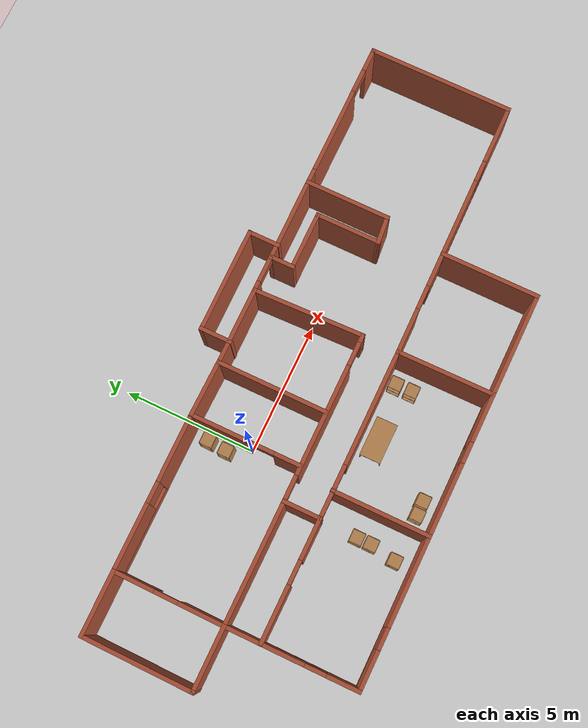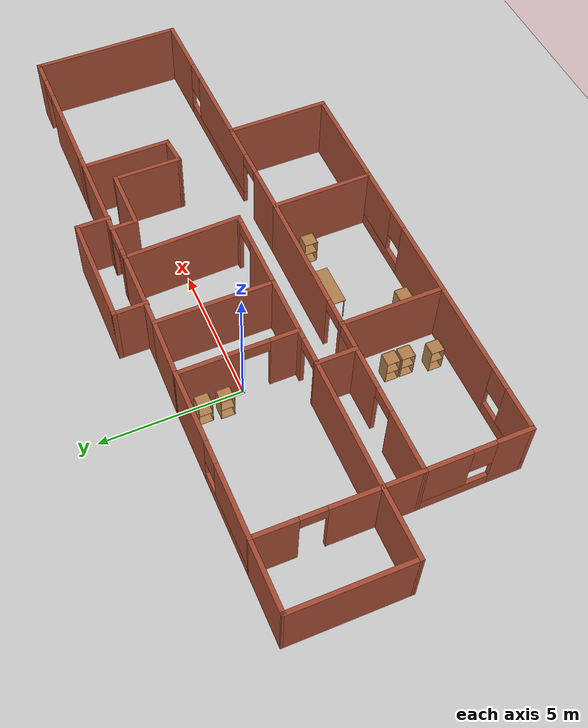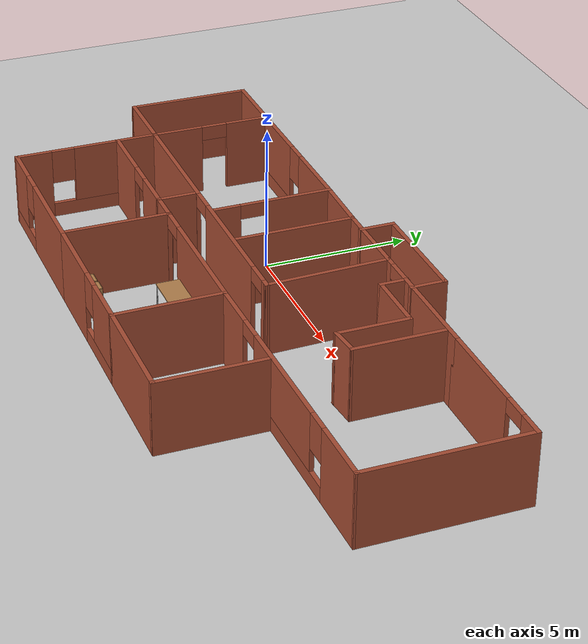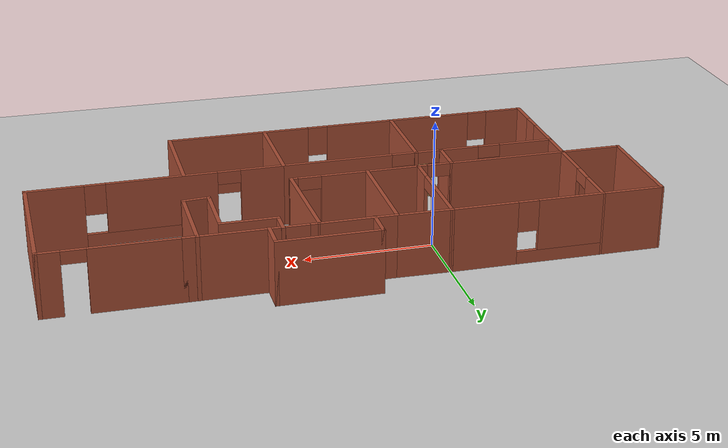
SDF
<sdf version="1.7">
 <world name="default">
  <light name="sun" type="directional">
   <pose>0 0 10 0 -0 0</pose>
   <diffuse>0.8 0.8 0.8 1</diffuse>
   <specular>0.2 0.2 0.2 1</specular>
   <attenuation>
    <range>1000</range>
    <constant>0.9</constant>
    <linear>0.01</linear>
    <quadratic>0.001</quadratic>
   </attenuation>
   <direction>-0.5 0.1 -0.9</direction>
   <spot><inner_angle>0</inner_angle><outer_angle>0</outer_angle><falloff>0</falloff></spot>
  </light>
  <model name="ground_plane">
   <static>1</static>
   <link name="link">
    <collision name="collision">
     <geometry><plane><normal>0 0 1</normal><size>100 100</size></plane></geometry>
     <surface><friction><ode><mu>100</mu><mu2>50</mu2></ode></friction></surface>
    </collision>
    <visual name="visual">
     <cast_shadows>0</cast_shadows>
     <geometry><plane><normal>0 0 1</normal><size>100 100</size></plane></geometry>
     <material>
      <script><uri>file://media/materials/scripts/gazebo.material</uri><name>Gazebo/Grey</name></script>
     </material>
    </visual>
   </link>
  </model>
  <gravity>0 0 -9.8</gravity>
  <magnetic_field>6e-06 2.3e-05 -4.2e-05</magnetic_field>
  <atmosphere type="adiabatic"/>
  <physics type="ode">
   <max_step_size>0.001</max_step_size>
   <real_time_factor>1</real_time_factor>
   <real_time_update_rate>1000</real_time_update_rate>
  </physics>
  <scene><ambient>0.4 0.4 0.4 1</ambient><background>0.7 0.7 0.7 1</background><shadows>1</shadows></scene>
  <audio><device>default</device></audio>
  <spherical_coordinates>
   <surface_model>EARTH_WGS84</surface_model>
   <latitude_deg>0</latitude_deg>
   <longitude_deg>0</longitude_deg>
   <elevation>0</elevation>
   <heading_deg>0</heading_deg>
  </spherical_coordinates>
  <model name="test_world">
   <pose>3.29981 -1.81395 0 0 -0 0</pose>
   <link name="Wall_0">
    <collision name="Wall_0_Collision">
     <geometry><box><size>1.5 0.15 2.5</size></box></geometry>
     <pose>0 0 1.25 0 -0 0</pose>
    </collision>
    <visual name="Wall_0_Visual">
     <pose>0 0 1.25 0 -0 0</pose>
     <geometry><box><size>1.5 0.15 2.5</size></box></geometry>
     <material>
      <script><uri>file://media/materials/scripts/gazebo.material</uri><name>Gazebo/Bricks</name></script>
      <ambient>1 1 1 1</ambient>
     </material>
     <meta><layer>0</layer></meta>
    </visual>
    <pose>-4.62561 -0.796372 0 0 -0 1.5708</pose>
   </link>
   <link name="Wall_1">
    <pose>-1.45061 -0.121372 0 0 -0 0</pose>
    <visual name="Wall_1_Visual_0">
     <pose>-3.1725 0 1.25 0 -0 0</pose>
     <geometry><box><size>0.155 0.15 2.5</size></box></geometry>
     <material>
      <script><uri>file://media/materials/scripts/gazebo.material</uri><name>Gazebo/Bricks</name></script>
      <ambient>1 1 1 1</ambient>
     </material>
     <meta><layer>0</layer></meta>
    </visual>
    <collision name="Wall_1_Collision_0">
     <geometry><box><size>0.155 0.15 2.5</size></box></geometry>
     <pose>-3.1725 0 1.25 0 -0 0</pose>
    </collision>
    <visual name="Wall_1_Visual_1">
     <pose>-0.091888 0 1.25 0 -0 0</pose>
     <geometry><box><size>4.20622 0.15 2.5</size></box></geometry>
     <material>
      <script><uri>file://media/materials/scripts/gazebo.material</uri><name>Gazebo/Bricks</name></script>
      <ambient>1 1 1 1</ambient>
     </material>
     <meta><layer>0</layer></meta>
    </visual>
    <collision name="Wall_1_Collision_1">
     <geometry><box><size>4.20622 0.15 2.5</size></box></geometry>
     <pose>-0.091888 0 1.25 0 -0 0</pose>
    </collision>
    <visual name="Wall_1_Visual_2">
     <pose>3.08061 0 1.25 0 -0 0</pose>
     <geometry><box><size>0.338776 0.15 2.5</size></box></geometry>
     <material>
      <script><uri>file://media/materials/scripts/gazebo.material</uri><name>Gazebo/Bricks</name></script>
      <ambient>1 1 1 1</ambient>
     </material>
     <meta><layer>0</layer></meta>
    </visual>
    <collision name="Wall_1_Collision_2">
     <geometry><box><size>0.338776 0.15 2.5</size></box></geometry>
     <pose>3.08061 0 1.25 0 -0 0</pose>
    </collision>
    <visual name="Wall_1_Visual_3">
     <pose>-2.645 0 2.25 0 -0 0</pose>
     <geometry><box><size>0.9 0.15 0.5</size></box></geometry>
     <material>
      <script><uri>file://media/materials/scripts/gazebo.material</uri><name>Gazebo/Bricks</name></script>
      <ambient>1 1 1 1</ambient>
     </material>
     <meta><layer>0</layer></meta>
    </visual>
    <collision name="Wall_1_Collision_3">
     <geometry><box><size>0.9 0.15 0.5</size></box></geometry>
     <pose>-2.645 0 2.25 0 -0 0</pose>
    </collision>
    <visual name="Wall_1_Visual_4">
     <pose>2.46122 0 2.25 0 -0 0</pose>
     <geometry><box><size>0.9 0.15 0.5</size></box></geometry>
     <material>
      <script><uri>file://media/materials/scripts/gazebo.material</uri><name>Gazebo/Bricks</name></script>
      <ambient>1 1 1 1</ambient>
     </material>
     <meta><layer>0</layer></meta>
    </visual>
    <collision name="Wall_1_Collision_4">
     <geometry><box><size>0.9 0.15 0.5</size></box></geometry>
     <pose>2.46122 0 2.25 0 -0 0</pose>
    </collision>
   </link>
   <link name="Wall_10">
    <collision name="Wall_10_Collision">
     <geometry><box><size>3.75 0.15 2.5</size></box></geometry>
     <pose>0 0 1.25 0 -0 0</pose>
    </collision>
    <visual name="Wall_10_Visual">
     <pose>0 0 1.25 0 -0 0</pose>
     <geometry><box><size>3.75 0.15 2.5</size></box></geometry>
     <material>
      <script><uri>file://media/materials/scripts/gazebo.material</uri><name>Gazebo/Bricks</name></script>
      <ambient>1 1 1 1</ambient>
     </material>
     <meta><layer>0</layer></meta>
    </visual>
    <pose>-3.59781 -3.25555 0 0 -0 -1.5708</pose>
   </link>
   <link name="Wall_11">
    <pose>-6.39781 -5.05555 0 0 -0 3.14159</pose>
    <visual name="Wall_11_Visual_0">
     <pose>-1.17433 0 1.25 0 -0 0</pose>
     <geometry><box><size>3.40134 0.15 2.5</size></box></geometry>
     <material>
      <script><uri>file://media/materials/scripts/gazebo.material</uri><name>Gazebo/Bricks</name></script>
      <ambient>1 1 1 1</ambient>
     </material>
     <meta><layer>0</layer></meta>
    </visual>
    <collision name="Wall_11_Collision_0">
     <geometry><box><size>3.40134 0.15 2.5</size></box></geometry>
     <pose>-1.17433 0 1.25 0 -0 0</pose>
    </collision>
    <visual name="Wall_11_Visual_1">
     <pose>1.70067 0 0.25 0 -0 0</pose>
     <geometry><box><size>2.34866 0.15 0.5</size></box></geometry>
     <material>
      <script><uri>file://media/materials/scripts/gazebo.material</uri><name>Gazebo/Bricks</name></script>
      <ambient>1 1 1 1</ambient>
     </material>
     <meta><layer>0</layer></meta>
    </visual>
    <collision name="Wall_11_Collision_1">
     <geometry><box><size>2.34866 0.15 0.5</size></box></geometry>
     <pose>1.70067 0 0.25 0 -0 0</pose>
    </collision>
    <visual name="Wall_11_Visual_2">
     <pose>2.10067 0 1.5 0 -0 0</pose>
     <geometry><box><size>1.54866 0.15 2</size></box></geometry>
     <material>
      <script><uri>file://media/materials/scripts/gazebo.material</uri><name>Gazebo/Bricks</name></script>
      <ambient>1 1 1 1</ambient>
     </material>
     <meta><layer>0</layer></meta>
    </visual>
    <collision name="Wall_11_Collision_2">
     <geometry><box><size>1.54866 0.15 2</size></box></geometry>
     <pose>2.10067 0 1.5 0 -0 0</pose>
    </collision>
    <visual name="Wall_11_Visual_3">
     <pose>0.926338 0 1.9 0 -0 0</pose>
     <geometry><box><size>0.8 0.15 1.2</size></box></geometry>
     <material>
      <script><uri>file://media/materials/scripts/gazebo.material</uri><name>Gazebo/Bricks</name></script>
      <ambient>1 1 1 1</ambient>
     </material>
     <meta><layer>0</layer></meta>
    </visual>
    <collision name="Wall_11_Collision_3">
     <geometry><box><size>0.8 0.15 1.2</size></box></geometry>
     <pose>0.926338 0 1.9 0 -0 0</pose>
    </collision>
   </link>
   <link name="Wall_12">
    <pose>-9.19781 -3.25555 0 0 -0 1.5708</pose>
    <visual name="Wall_12_Visual_0">
     <pose>-1.23439 0 1.25 0 -0 0</pose>
     <geometry><box><size>1.28121 0.15 2.5</size></box></geometry>
     <material>
      <script><uri>file://media/materials/scripts/gazebo.material</uri><name>Gazebo/Bricks</name></script>
      <ambient>1 1 1 1</ambient>
     </material>
     <meta><layer>0</layer></meta>
    </visual>
    <collision name="Wall_12_Collision_0">
     <geometry><box><size>1.28121 0.15 2.5</size></box></geometry>
     <pose>-1.23439 0 1.25 0 -0 0</pose>
    </collision>
    <visual name="Wall_12_Visual_1">
     <pose>0.640607 0 0.25 0 -0 0</pose>
     <geometry><box><size>2.46879 0.15 0.5</size></box></geometry>
     <material>
      <script><uri>file://media/materials/scripts/gazebo.material</uri><name>Gazebo/Bricks</name></script>
      <ambient>1 1 1 1</ambient>
     </material>
     <meta><layer>0</layer></meta>
    </visual>
    <collision name="Wall_12_Collision_1">
     <geometry><box><size>2.46879 0.15 0.5</size></box></geometry>
     <pose>0.640607 0 0.25 0 -0 0</pose>
    </collision>
    <visual name="Wall_12_Visual_2">
     <pose>1.04061 0 1.5 0 -0 0</pose>
     <geometry><box><size>1.66879 0.15 2</size></box></geometry>
     <material>
      <script><uri>file://media/materials/scripts/gazebo.material</uri><name>Gazebo/Bricks</name></script>
      <ambient>1 1 1 1</ambient>
     </material>
     <meta><layer>0</layer></meta>
    </visual>
    <collision name="Wall_12_Collision_2">
     <geometry><box><size>1.66879 0.15 2</size></box></geometry>
     <pose>1.04061 0 1.5 0 -0 0</pose>
    </collision>
    <visual name="Wall_12_Visual_3">
     <pose>-0.193786 0 1.9 0 -0 0</pose>
     <geometry><box><size>0.8 0.15 1.2</size></box></geometry>
     <material>
      <script><uri>file://media/materials/scripts/gazebo.material</uri><name>Gazebo/Bricks</name></script>
      <ambient>1 1 1 1</ambient>
     </material>
     <meta><layer>0</layer></meta>
    </visual>
    <collision name="Wall_12_Collision_3">
     <geometry><box><size>0.8 0.15 1.2</size></box></geometry>
     <pose>-0.193786 0 1.9 0 -0 0</pose>
    </collision>
   </link>
   <link name="Wall_13">
    <pose>-6.91171 -1.46346 0 0 -0 -0.00346</pose>
    <visual name="Wall_13_Visual_0">
     <pose>-1.25332 0 1.25 0 -0 0</pose>
     <geometry><box><size>2.21558 0.15 2.5</size></box></geometry>
     <material>
      <script><uri>file://media/materials/scripts/gazebo.material</uri><name>Gazebo/Bricks</name></script>
      <ambient>1 1 1 1</ambient>
     </material>
     <meta><layer>0</layer></meta>
    </visual>
    <collision name="Wall_13_Collision_0">
     <geometry><box><size>2.21558 0.15 2.5</size></box></geometry>
     <pose>-1.25332 0 1.25 0 -0 0</pose>
    </collision>
    <visual name="Wall_13_Visual_1">
     <pose>1.55779 0 1.25 0 -0 0</pose>
     <geometry><box><size>1.60664 0.15 2.5</size></box></geometry>
     <material>
      <script><uri>file://media/materials/scripts/gazebo.material</uri><name>Gazebo/Bricks</name></script>
      <ambient>1 1 1 1</ambient>
     </material>
     <meta><layer>0</layer></meta>
    </visual>
    <collision name="Wall_13_Collision_1">
     <geometry><box><size>1.60664 0.15 2.5</size></box></geometry>
     <pose>1.55779 0 1.25 0 -0 0</pose>
    </collision>
    <visual name="Wall_13_Visual_2">
     <pose>0.304473 0 2.25 0 -0 0</pose>
     <geometry><box><size>0.9 0.15 0.5</size></box></geometry>
     <material>
      <script><uri>file://media/materials/scripts/gazebo.material</uri><name>Gazebo/Bricks</name></script>
      <ambient>1 1 1 1</ambient>
     </material>
     <meta><layer>0</layer></meta>
    </visual>
    <collision name="Wall_13_Collision_2">
     <geometry><box><size>0.9 0.15 0.5</size></box></geometry>
     <pose>0.304473 0 2.25 0 -0 0</pose>
    </collision>
   </link>
   <link name="Wall_15">
    <collision name="Wall_15_Collision">
     <geometry><box><size>1.5 0.15 2.5</size></box></geometry>
     <pose>0 0 1.25 0 -0 0</pose>
    </collision>
    <visual name="Wall_15_Visual">
     <pose>0 0 1.25 0 -0 0</pose>
     <geometry><box><size>1.5 0.15 2.5</size></box></geometry>
     <material>
      <script><uri>file://media/materials/scripts/gazebo.material</uri><name>Gazebo/Bricks</name></script>
      <ambient>1 1 1 1</ambient>
     </material>
     <meta><layer>0</layer></meta>
    </visual>
    <pose>-9.19781 -0.780551 0 0 -0 1.5708</pose>
   </link>
   <link name="Wall_16">
    <collision name="Wall_16_Collision">
     <geometry><box><size>4.72222 0.15 2.5</size></box></geometry>
     <pose>0 0 1.25 0 -0 0</pose>
    </collision>
    <visual name="Wall_16_Visual">
     <pose>0 0 1.25 0 -0 0</pose>
     <geometry><box><size>4.72222 0.15 2.5</size></box></geometry>
     <material>
      <script><uri>file://media/materials/scripts/gazebo.material</uri><name>Gazebo/Bricks</name></script>
      <ambient>1 1 1 1</ambient>
     </material>
     <meta><layer>0</layer></meta>
    </visual>
    <pose>-6.91171 -0.113462 0 0 -0 -0.00346</pose>
   </link>
   <link name="Wall_18">
    <pose>-0.922808 -5.05555 0 0 -0 0</pose>
    <visual name="Wall_18_Visual_0">
     <pose>-1.34867 0 1.25 0 -0 0</pose>
     <geometry><box><size>2.80266 0.15 2.5</size></box></geometry>
     <material>
      <script><uri>file://media/materials/scripts/gazebo.material</uri><name>Gazebo/Bricks</name></script>
      <ambient>1 1 1 1</ambient>
     </material>
     <meta><layer>0</layer></meta>
    </visual>
    <collision name="Wall_18_Collision_0">
     <geometry><box><size>2.80266 0.15 2.5</size></box></geometry>
     <pose>-1.34867 0 1.25 0 -0 0</pose>
    </collision>
    <visual name="Wall_18_Visual_1">
     <pose>1.40133 0 0.25 0 -0 0</pose>
     <geometry><box><size>2.69734 0.15 0.5</size></box></geometry>
     <material>
      <script><uri>file://media/materials/scripts/gazebo.material</uri><name>Gazebo/Bricks</name></script>
      <ambient>1 1 1 1</ambient>
     </material>
     <meta><layer>0</layer></meta>
    </visual>
    <collision name="Wall_18_Collision_1">
     <geometry><box><size>2.69734 0.15 0.5</size></box></geometry>
     <pose>1.40133 0 0.25 0 -0 0</pose>
    </collision>
    <visual name="Wall_18_Visual_2">
     <pose>1.80133 0 1.5 0 -0 0</pose>
     <geometry><box><size>1.89734 0.15 2</size></box></geometry>
     <material>
      <script><uri>file://media/materials/scripts/gazebo.material</uri><name>Gazebo/Bricks</name></script>
      <ambient>1 1 1 1</ambient>
     </material>
     <meta><layer>0</layer></meta>
    </visual>
    <collision name="Wall_18_Collision_2">
     <geometry><box><size>1.89734 0.15 2</size></box></geometry>
     <pose>1.80133 0 1.5 0 -0 0</pose>
    </collision>
    <visual name="Wall_18_Visual_3">
     <pose>0.452662 0 1.9 0 -0 0</pose>
     <geometry><box><size>0.8 0.15 1.2</size></box></geometry>
     <material>
      <script><uri>file://media/materials/scripts/gazebo.material</uri><name>Gazebo/Bricks</name></script>
      <ambient>1 1 1 1</ambient>
     </material>
     <meta><layer>0</layer></meta>
    </visual>
    <collision name="Wall_18_Collision_3">
     <geometry><box><size>0.8 0.15 1.2</size></box></geometry>
     <pose>0.452662 0 1.9 0 -0 0</pose>
    </collision>
   </link>
   <link name="Wall_19">
    <collision name="Wall_19_Collision">
     <geometry><box><size>3.73429 0.15 2.5</size></box></geometry>
     <pose>0 0 1.25 0 -0 0</pose>
    </collision>
    <visual name="Wall_19_Visual">
     <pose>0 0 1.25 0 -0 0</pose>
     <geometry><box><size>3.73429 0.15 2.5</size></box></geometry>
     <material>
      <script><uri>file://media/materials/scripts/gazebo.material</uri><name>Gazebo/Bricks</name></script>
      <ambient>1 1 1 1</ambient>
     </material>
     <meta><layer>0</layer></meta>
    </visual>
    <pose>1.73829 -3.26346 0 0 -0 1.57855</pose>
   </link>
   <link name="Wall_21">
    <pose>-3.30016 1.97869 0 0 -0 1.5708</pose>
    <visual name="Wall_21_Visual_0">
     <pose>-1.60951 0 1.25 0 -0 0</pose>
     <geometry><box><size>1.03098 0.15 2.5</size></box></geometry>
     <material>
      <script><uri>file://media/materials/scripts/gazebo.material</uri><name>Gazebo/Bricks</name></script>
      <ambient>1 1 1 1</ambient>
     </material>
     <meta><layer>0</layer></meta>
    </visual>
    <collision name="Wall_21_Collision_0">
     <geometry><box><size>1.03098 0.15 2.5</size></box></geometry>
     <pose>-1.60951 0 1.25 0 -0 0</pose>
    </collision>
    <visual name="Wall_21_Visual_1">
     <pose>0.965488 0 1.25 0 -0 0</pose>
     <geometry><box><size>2.31902 0.15 2.5</size></box></geometry>
     <material>
      <script><uri>file://media/materials/scripts/gazebo.material</uri><name>Gazebo/Bricks</name></script>
      <ambient>1 1 1 1</ambient>
     </material>
     <meta><layer>0</layer></meta>
    </visual>
    <collision name="Wall_21_Collision_1">
     <geometry><box><size>2.31902 0.15 2.5</size></box></geometry>
     <pose>0.965488 0 1.25 0 -0 0</pose>
    </collision>
    <visual name="Wall_21_Visual_2">
     <pose>-0.644024 0 2.25 0 -0 0</pose>
     <geometry><box><size>0.9 0.15 0.5</size></box></geometry>
     <material>
      <script><uri>file://media/materials/scripts/gazebo.material</uri><name>Gazebo/Bricks</name></script>
      <ambient>1 1 1 1</ambient>
     </material>
     <meta><layer>0</layer></meta>
    </visual>
    <collision name="Wall_21_Collision_2">
     <geometry><box><size>0.9 0.15 0.5</size></box></geometry>
     <pose>-0.644024 0 2.25 0 -0 0</pose>
    </collision>
   </link>
   <link name="Wall_22">
    <pose>-6.22516 4.02869 0 0 -0 3.14159</pose>
    <visual name="Wall_22_Visual_0">
     <pose>-1.69302 0 1.25 0 -0 0</pose>
     <geometry><box><size>2.61396 0.15 2.5</size></box></geometry>
     <material>
      <script><uri>file://media/materials/scripts/gazebo.material</uri><name>Gazebo/Bricks</name></script>
      <ambient>1 1 1 1</ambient>
     </material>
     <meta><layer>0</layer></meta>
    </visual>
    <collision name="Wall_22_Collision_0">
     <geometry><box><size>2.61396 0.15 2.5</size></box></geometry>
     <pose>-1.69302 0 1.25 0 -0 0</pose>
    </collision>
    <visual name="Wall_22_Visual_1">
     <pose>1.30698 0 0.25 0 -0 0</pose>
     <geometry><box><size>3.38604 0.15 0.5</size></box></geometry>
     <material>
      <script><uri>file://media/materials/scripts/gazebo.material</uri><name>Gazebo/Bricks</name></script>
      <ambient>1 1 1 1</ambient>
     </material>
     <meta><layer>0</layer></meta>
    </visual>
    <collision name="Wall_22_Collision_1">
     <geometry><box><size>3.38604 0.15 0.5</size></box></geometry>
     <pose>1.30698 0 0.25 0 -0 0</pose>
    </collision>
    <visual name="Wall_22_Visual_2">
     <pose>1.70698 0 1.5 0 -0 0</pose>
     <geometry><box><size>2.58604 0.15 2</size></box></geometry>
     <material>
      <script><uri>file://media/materials/scripts/gazebo.material</uri><name>Gazebo/Bricks</name></script>
      <ambient>1 1 1 1</ambient>
     </material>
     <meta><layer>0</layer></meta>
    </visual>
    <collision name="Wall_22_Collision_2">
     <geometry><box><size>2.58604 0.15 2</size></box></geometry>
     <pose>1.70698 0 1.5 0 -0 0</pose>
    </collision>
    <visual name="Wall_22_Visual_3">
     <pose>0.013957 0 1.9 0 -0 0</pose>
     <geometry><box><size>0.8 0.15 1.2</size></box></geometry>
     <material>
      <script><uri>file://media/materials/scripts/gazebo.material</uri><name>Gazebo/Bricks</name></script>
      <ambient>1 1 1 1</ambient>
     </material>
     <meta><layer>0</layer></meta>
    </visual>
    <collision name="Wall_22_Collision_3">
     <geometry><box><size>0.8 0.15 1.2</size></box></geometry>
     <pose>0.013957 0 1.9 0 -0 0</pose>
    </collision>
   </link>
   <link name="Wall_23">
    <pose>-9.17398 1.96157 0 0 -0 -1.58232</pose>
    <visual name="Wall_23_Visual_0">
     <pose>-1.34939 0 1.25 0 -0 0</pose>
     <geometry><box><size>1.58574 0.15 2.5</size></box></geometry>
     <material>
      <script><uri>file://media/materials/scripts/gazebo.material</uri><name>Gazebo/Bricks</name></script>
      <ambient>1 1 1 1</ambient>
     </material>
     <meta><layer>0</layer></meta>
    </visual>
    <collision name="Wall_23_Collision_0">
     <geometry><box><size>1.58574 0.15 2.5</size></box></geometry>
     <pose>-1.34939 0 1.25 0 -0 0</pose>
    </collision>
    <visual name="Wall_23_Visual_1">
     <pose>1.24287 0 1.25 0 -0 0</pose>
     <geometry><box><size>1.79878 0.15 2.5</size></box></geometry>
     <material>
      <script><uri>file://media/materials/scripts/gazebo.material</uri><name>Gazebo/Bricks</name></script>
      <ambient>1 1 1 1</ambient>
     </material>
     <meta><layer>0</layer></meta>
    </visual>
    <collision name="Wall_23_Collision_1">
     <geometry><box><size>1.79878 0.15 2.5</size></box></geometry>
     <pose>1.24287 0 1.25 0 -0 0</pose>
    </collision>
    <visual name="Wall_23_Visual_2">
     <pose>-0.10652 0 2.25 0 -0 0</pose>
     <geometry><box><size>0.9 0.15 0.5</size></box></geometry>
     <material>
      <script><uri>file://media/materials/scripts/gazebo.material</uri><name>Gazebo/Bricks</name></script>
      <ambient>1 1 1 1</ambient>
     </material>
     <meta><layer>0</layer></meta>
    </visual>
    <collision name="Wall_23_Collision_2">
     <geometry><box><size>0.9 0.15 0.5</size></box></geometry>
     <pose>-0.10652 0 2.25 0 -0 0</pose>
    </collision>
   </link>
   <link name="Wall_25">
    <collision name="Wall_25_Collision">
     <geometry><box><size>2.5 0.15 2.5</size></box></geometry>
     <pose>0 0 1.25 0 -0 0</pose>
    </collision>
    <visual name="Wall_25_Visual">
     <pose>0 0 1.25 0 -0 0</pose>
     <geometry><box><size>2.5 0.15 2.5</size></box></geometry>
     <material>
      <script><uri>file://media/materials/scripts/gazebo.material</uri><name>Gazebo/Bricks</name></script>
      <ambient>1 1 1 1</ambient>
     </material>
     <meta><layer>0</layer></meta>
    </visual>
    <pose>-10.3252 4.02869 0 0 -0 3.14159</pose>
   </link>
   <link name="Wall_29">
    <collision name="Wall_29_Collision">
     <geometry><box><size>2.5 0.15 2.5</size></box></geometry>
     <pose>0 0 1.25 0 -0 0</pose>
    </collision>
    <visual name="Wall_29_Visual">
     <pose>0 0 1.25 0 -0 0</pose>
     <geometry><box><size>2.5 0.15 2.5</size></box></geometry>
     <material>
      <script><uri>file://media/materials/scripts/gazebo.material</uri><name>Gazebo/Bricks</name></script>
      <ambient>1 1 1 1</ambient>
     </material>
     <meta><layer>0</layer></meta>
    </visual>
    <pose>-10.3728 -0.105551 0 0 -0 3.14159</pose>
   </link>
   <link name="Wall_3">
    <pose>-1.45061 -1.47137 0 0 -0 0</pose>
    <visual name="Wall_3_Visual_0">
     <pose>-3.1725 0 1.25 0 -0 0</pose>
     <geometry><box><size>0.155 0.15 2.5</size></box></geometry>
     <material>
      <script><uri>file://media/materials/scripts/gazebo.material</uri><name>Gazebo/Bricks</name></script>
      <ambient>1 1 1 1</ambient>
     </material>
     <meta><layer>0</layer></meta>
    </visual>
    <collision name="Wall_3_Collision_0">
     <geometry><box><size>0.155 0.15 2.5</size></box></geometry>
     <pose>-3.1725 0 1.25 0 -0 0</pose>
    </collision>
    <visual name="Wall_3_Visual_1">
     <pose>-2.13145 0 1.25 0 -0 0</pose>
     <geometry><box><size>0.127105 0.15 2.5</size></box></geometry>
     <material>
      <script><uri>file://media/materials/scripts/gazebo.material</uri><name>Gazebo/Bricks</name></script>
      <ambient>1 1 1 1</ambient>
     </material>
     <meta><layer>0</layer></meta>
    </visual>
    <collision name="Wall_3_Collision_1">
     <geometry><box><size>0.127105 0.15 2.5</size></box></geometry>
     <pose>-2.13145 0 1.25 0 -0 0</pose>
    </collision>
    <visual name="Wall_3_Visual_2">
     <pose>1.04105 0 1.25 0 -0 0</pose>
     <geometry><box><size>4.41789 0.15 2.5</size></box></geometry>
     <material>
      <script><uri>file://media/materials/scripts/gazebo.material</uri><name>Gazebo/Bricks</name></script>
      <ambient>1 1 1 1</ambient>
     </material>
     <meta><layer>0</layer></meta>
    </visual>
    <collision name="Wall_3_Collision_2">
     <geometry><box><size>4.41789 0.15 2.5</size></box></geometry>
     <pose>1.04105 0 1.25 0 -0 0</pose>
    </collision>
    <visual name="Wall_3_Visual_3">
     <pose>-2.645 0 2.25 0 -0 0</pose>
     <geometry><box><size>0.9 0.15 0.5</size></box></geometry>
     <material>
      <script><uri>file://media/materials/scripts/gazebo.material</uri><name>Gazebo/Bricks</name></script>
      <ambient>1 1 1 1</ambient>
     </material>
     <meta><layer>0</layer></meta>
    </visual>
    <collision name="Wall_3_Collision_3">
     <geometry><box><size>0.9 0.15 0.5</size></box></geometry>
     <pose>-2.645 0 2.25 0 -0 0</pose>
    </collision>
    <visual name="Wall_3_Visual_4">
     <pose>-1.6179 0 2.25 0 -0 0</pose>
     <geometry><box><size>0.9 0.15 0.5</size></box></geometry>
     <material>
      <script><uri>file://media/materials/scripts/gazebo.material</uri><name>Gazebo/Bricks</name></script>
      <ambient>1 1 1 1</ambient>
     </material>
     <meta><layer>0</layer></meta>
    </visual>
    <collision name="Wall_3_Collision_4">
     <geometry><box><size>0.9 0.15 0.5</size></box></geometry>
     <pose>-1.6179 0 2.25 0 -0 0</pose>
    </collision>
   </link>
   <link name="Wall_30">
    <collision name="Wall_30_Collision">
     <geometry><box><size>4.28451 0.15 2.5</size></box></geometry>
     <pose>0 0 1.25 0 -0 0</pose>
    </collision>
    <visual name="Wall_30_Visual">
     <pose>0 0 1.25 0 -0 0</pose>
     <geometry><box><size>4.28451 0.15 2.5</size></box></geometry>
     <material>
      <script><uri>file://media/materials/scripts/gazebo.material</uri><name>Gazebo/Bricks</name></script>
      <ambient>1 1 1 1</ambient>
     </material>
     <meta><layer>0</layer></meta>
    </visual>
    <pose>-11.524 1.96157 0 0 -0 1.55927</pose>
   </link>
   <link name="Wall_32">
    <collision name="Wall_32_Collision">
     <geometry><box><size>4.25 0.15 2.5</size></box></geometry>
     <pose>0 0 1.25 0 -0 0</pose>
    </collision>
    <visual name="Wall_32_Visual">
     <pose>0 0 1.25 0 -0 0</pose>
     <geometry><box><size>4.25 0.15 2.5</size></box></geometry>
     <material>
      <script><uri>file://media/materials/scripts/gazebo.material</uri><name>Gazebo/Bricks</name></script>
      <ambient>1 1 1 1</ambient>
     </material>
     <meta><layer>0</layer></meta>
    </visual>
    <pose>-1.25215 1.93566 0 0 -0 1.5708</pose>
   </link>
   <link name="Wall_33">
    <collision name="Wall_33_Collision">
     <geometry><box><size>2.19847 0.15 2.5</size></box></geometry>
     <pose>0 0 1.25 0 -0 0</pose>
    </collision>
    <visual name="Wall_33_Visual">
     <pose>0 0 1.25 0 -0 0</pose>
     <geometry><box><size>2.19847 0.15 2.5</size></box></geometry>
     <material>
      <script><uri>file://media/materials/scripts/gazebo.material</uri><name>Gazebo/Bricks</name></script>
      <ambient>1 1 1 1</ambient>
     </material>
     <meta><layer>0</layer></meta>
    </visual>
    <pose>-2.27615 4.00718 0 0 -0 3.12059</pose>
   </link>
   <link name="Wall_35">
    <collision name="Wall_35_Collision">
     <geometry><box><size>3 0.15 2.5</size></box></geometry>
     <pose>0 0 1.25 0 -0 0</pose>
    </collision>
    <visual name="Wall_35_Visual">
     <pose>0 0 1.25 0 -0 0</pose>
     <geometry><box><size>3 0.15 2.5</size></box></geometry>
     <material>
      <script><uri>file://media/materials/scripts/gazebo.material</uri><name>Gazebo/Bricks</name></script>
      <ambient>1 1 1 1</ambient>
     </material>
     <meta><layer>0</layer></meta>
    </visual>
    <pose>0.172854 3.98566 0 0 -0 0</pose>
   </link>
   <link name="Wall_36">
    <collision name="Wall_36_Collision">
     <geometry><box><size>4.25898 0.15 2.5</size></box></geometry>
     <pose>0 0 1.25 0 -0 0</pose>
    </collision>
    <visual name="Wall_36_Visual">
     <pose>0 0 1.25 0 -0 0</pose>
     <geometry><box><size>4.25898 0.15 2.5</size></box></geometry>
     <material>
      <script><uri>file://media/materials/scripts/gazebo.material</uri><name>Gazebo/Bricks</name></script>
      <ambient>1 1 1 1</ambient>
     </material>
     <meta><layer>0</layer></meta>
    </visual>
    <pose>1.66112 1.93215 0 0 -0 -1.54</pose>
   </link>
   <link name="Wall_38">
    <pose>4.02285 3.98566 0 0 -0 0</pose>
    <visual name="Wall_38_Visual_0">
     <pose>-2.28928 0 1.25 0 -0 0</pose>
     <geometry><box><size>0.421438 0.15 2.5</size></box></geometry>
     <material>
      <script><uri>file://media/materials/scripts/gazebo.material</uri><name>Gazebo/Bricks</name></script>
      <ambient>1 1 1 1</ambient>
     </material>
     <meta><layer>0</layer></meta>
    </visual>
    <collision name="Wall_38_Collision_0">
     <geometry><box><size>0.421438 0.15 2.5</size></box></geometry>
     <pose>-2.28928 0 1.25 0 -0 0</pose>
    </collision>
    <visual name="Wall_38_Visual_1">
     <pose>0.660719 0 1.25 0 -0 0</pose>
     <geometry><box><size>3.67856 0.15 2.5</size></box></geometry>
     <material>
      <script><uri>file://media/materials/scripts/gazebo.material</uri><name>Gazebo/Bricks</name></script>
      <ambient>1 1 1 1</ambient>
     </material>
     <meta><layer>0</layer></meta>
    </visual>
    <collision name="Wall_38_Collision_1">
     <geometry><box><size>3.67856 0.15 2.5</size></box></geometry>
     <pose>0.660719 0 1.25 0 -0 0</pose>
    </collision>
    <visual name="Wall_38_Visual_2">
     <pose>-1.62856 0 2.25 0 -0 0</pose>
     <geometry><box><size>0.9 0.15 0.5</size></box></geometry>
     <material>
      <script><uri>file://media/materials/scripts/gazebo.material</uri><name>Gazebo/Bricks</name></script>
      <ambient>1 1 1 1</ambient>
     </material>
     <meta><layer>0</layer></meta>
    </visual>
    <collision name="Wall_38_Collision_2">
     <geometry><box><size>0.9 0.15 0.5</size></box></geometry>
     <pose>-1.62856 0 2.25 0 -0 0</pose>
    </collision>
   </link>
   <link name="Wall_41">
    <collision name="Wall_41_Collision">
     <geometry><box><size>1.25 0.15 2.5</size></box></geometry>
     <pose>0 0 1.25 0 -0 0</pose>
    </collision>
    <visual name="Wall_41_Visual">
     <pose>0 0 1.25 0 -0 0</pose>
     <geometry><box><size>1.25 0.15 2.5</size></box></geometry>
     <material>
      <script><uri>file://media/materials/scripts/gazebo.material</uri><name>Gazebo/Bricks</name></script>
      <ambient>1 1 1 1</ambient>
     </material>
     <meta><layer>0</layer></meta>
    </visual>
    <pose>-0.434536 4.50613 0 0 -0 1.5708</pose>
   </link>
   <link name="Wall_42">
    <collision name="Wall_42_Collision">
     <geometry><box><size>4 0.15 2.5</size></box></geometry>
     <pose>0 0 1.25 0 -0 0</pose>
    </collision>
    <visual name="Wall_42_Visual">
     <pose>0 0 1.25 0 -0 0</pose>
     <geometry><box><size>4 0.15 2.5</size></box></geometry>
     <material>
      <script><uri>file://media/materials/scripts/gazebo.material</uri><name>Gazebo/Bricks</name></script>
      <ambient>1 1 1 1</ambient>
     </material>
     <meta><layer>0</layer></meta>
    </visual>
    <pose>1.49046 5.05613 0 0 -0 0</pose>
   </link>
   <link name="Wall_45">
    <collision name="Wall_45_Collision">
     <geometry><box><size>1.25 0.15 2.5</size></box></geometry>
     <pose>0 0 1.25 0 -0 0</pose>
    </collision>
    <visual name="Wall_45_Visual">
     <pose>0 0 1.25 0 -0 0</pose>
     <geometry><box><size>1.25 0.15 2.5</size></box></geometry>
     <material>
      <script><uri>file://media/materials/scripts/gazebo.material</uri><name>Gazebo/Bricks</name></script>
      <ambient>1 1 1 1</ambient>
     </material>
     <meta><layer>0</layer></meta>
    </visual>
    <pose>3.41546 4.50613 0 0 -0 -1.5708</pose>
   </link>
   <link name="Wall_47">
    <pose>8.99785 3.98566 0 0 -0 0</pose>
    <visual name="Wall_47_Visual_0">
     <pose>-0.909562 0 1.25 0 -0 0</pose>
     <geometry><box><size>3.43088 0.15 2.5</size></box></geometry>
     <material>
      <script><uri>file://media/materials/scripts/gazebo.material</uri><name>Gazebo/Bricks</name></script>
      <ambient>1 1 1 1</ambient>
     </material>
     <meta><layer>0</layer></meta>
    </visual>
    <collision name="Wall_47_Collision_0">
     <geometry><box><size>3.43088 0.15 2.5</size></box></geometry>
     <pose>-0.909562 0 1.25 0 -0 0</pose>
    </collision>
    <visual name="Wall_47_Visual_1">
     <pose>2.16544 0 1.25 0 -0 0</pose>
     <geometry><box><size>0.919123 0.15 2.5</size></box></geometry>
     <material>
      <script><uri>file://media/materials/scripts/gazebo.material</uri><name>Gazebo/Bricks</name></script>
      <ambient>1 1 1 1</ambient>
     </material>
     <meta><layer>0</layer></meta>
    </visual>
    <collision name="Wall_47_Collision_1">
     <geometry><box><size>0.919123 0.15 2.5</size></box></geometry>
     <pose>2.16544 0 1.25 0 -0 0</pose>
    </collision>
    <visual name="Wall_47_Visual_2">
     <pose>1.25588 0 2.25 0 -0 0</pose>
     <geometry><box><size>0.9 0.15 0.5</size></box></geometry>
     <material>
      <script><uri>file://media/materials/scripts/gazebo.material</uri><name>Gazebo/Bricks</name></script>
      <ambient>1 1 1 1</ambient>
     </material>
     <meta><layer>0</layer></meta>
    </visual>
    <collision name="Wall_47_Collision_2">
     <geometry><box><size>0.9 0.15 0.5</size></box></geometry>
     <pose>1.25588 0 2.25 0 -0 0</pose>
    </collision>
   </link>
   <link name="Wall_48">
    <collision name="Wall_48_Collision">
     <geometry><box><size>5.5 0.15 2.5</size></box></geometry>
     <pose>0 0 1.25 0 -0 0</pose>
    </collision>
    <visual name="Wall_48_Visual">
     <pose>0 0 1.25 0 -0 0</pose>
     <geometry><box><size>5.5 0.15 2.5</size></box></geometry>
     <material>
      <script><uri>file://media/materials/scripts/gazebo.material</uri><name>Gazebo/Bricks</name></script>
      <ambient>1 1 1 1</ambient>
     </material>
     <meta><layer>0</layer></meta>
    </visual>
    <pose>11.5479 1.31066 0 0 -0 -1.5708</pose>
   </link>
   <link name="Wall_49">
    <pose>6.63612 -1.41786 0 0 -0 -3.1307</pose>
    <visual name="Wall_49_Visual_0">
     <pose>-3.85978 0 1.25 0 -0 0</pose>
     <geometry><box><size>2.25449 0.15 2.5</size></box></geometry>
     <material>
      <script><uri>file://media/materials/scripts/gazebo.material</uri><name>Gazebo/Bricks</name></script>
      <ambient>1 1 1 1</ambient>
     </material>
     <meta><layer>0</layer></meta>
    </visual>
    <collision name="Wall_49_Collision_0">
     <geometry><box><size>2.25449 0.15 2.5</size></box></geometry>
     <pose>-3.85978 0 1.25 0 -0 0</pose>
    </collision>
    <visual name="Wall_49_Visual_1">
     <pose>4.10588 0 1.25 0 -0 0</pose>
     <geometry><box><size>1.7623 0.15 2.5</size></box></geometry>
     <material>
      <script><uri>file://media/materials/scripts/gazebo.material</uri><name>Gazebo/Bricks</name></script>
      <ambient>1 1 1 1</ambient>
     </material>
     <meta><layer>0</layer></meta>
    </visual>
    <collision name="Wall_49_Collision_1">
     <geometry><box><size>1.7623 0.15 2.5</size></box></geometry>
     <pose>4.10588 0 1.25 0 -0 0</pose>
    </collision>
    <visual name="Wall_49_Visual_2">
     <pose>-0.203906 0 0.25 0 -0 0</pose>
     <geometry><box><size>5.05727 0.15 0.5</size></box></geometry>
     <material>
      <script><uri>file://media/materials/scripts/gazebo.material</uri><name>Gazebo/Bricks</name></script>
      <ambient>1 1 1 1</ambient>
     </material>
     <meta><layer>0</layer></meta>
    </visual>
    <collision name="Wall_49_Collision_2">
     <geometry><box><size>5.05727 0.15 0.5</size></box></geometry>
     <pose>-0.203906 0 0.25 0 -0 0</pose>
    </collision>
    <visual name="Wall_49_Visual_3">
     <pose>0.196094 0 1.5 0 -0 0</pose>
     <geometry><box><size>4.25727 0.15 2</size></box></geometry>
     <material>
      <script><uri>file://media/materials/scripts/gazebo.material</uri><name>Gazebo/Bricks</name></script>
      <ambient>1 1 1 1</ambient>
     </material>
     <meta><layer>0</layer></meta>
    </visual>
    <collision name="Wall_49_Collision_3">
     <geometry><box><size>4.25727 0.15 2</size></box></geometry>
     <pose>0.196094 0 1.5 0 -0 0</pose>
    </collision>
    <visual name="Wall_49_Visual_4">
     <pose>-2.33254 0 1.9 0 -0 0</pose>
     <geometry><box><size>0.8 0.15 1.2</size></box></geometry>
     <material>
      <script><uri>file://media/materials/scripts/gazebo.material</uri><name>Gazebo/Bricks</name></script>
      <ambient>1 1 1 1</ambient>
     </material>
     <meta><layer>0</layer></meta>
    </visual>
    <collision name="Wall_49_Collision_4">
     <geometry><box><size>0.8 0.15 1.2</size></box></geometry>
     <pose>-2.33254 0 1.9 0 -0 0</pose>
    </collision>
    <visual name="Wall_49_Visual_5">
     <pose>2.77473 0 2.25 0 -0 0</pose>
     <geometry><box><size>0.9 0.15 0.5</size></box></geometry>
     <material>
      <script><uri>file://media/materials/scripts/gazebo.material</uri><name>Gazebo/Bricks</name></script>
      <ambient>1 1 1 1</ambient>
     </material>
     <meta><layer>0</layer></meta>
    </visual>
    <collision name="Wall_49_Collision_5">
     <geometry><box><size>0.9 0.15 0.5</size></box></geometry>
     <pose>2.77473 0 2.25 0 -0 0</pose>
    </collision>
   </link>
   <link name="Wall_51">
    <collision name="Wall_51_Collision">
     <geometry><box><size>3.25 0.15 2.5</size></box></geometry>
     <pose>0 0 1.25 0 -0 0</pose>
    </collision>
    <visual name="Wall_51_Visual">
     <pose>0 0 1.25 0 -0 0</pose>
     <geometry><box><size>3.25 0.15 2.5</size></box></geometry>
     <material>
      <script><uri>file://media/materials/scripts/gazebo.material</uri><name>Gazebo/Bricks</name></script>
      <ambient>1 1 1 1</ambient>
     </material>
     <meta><layer>0</layer></meta>
    </visual>
    <pose>5.98231 2.44015 0 0 -0 -1.5708</pose>
   </link>
   <link name="Wall_53">
    <collision name="Wall_53_Collision">
     <geometry><box><size>4 0.15 2.5</size></box></geometry>
     <pose>0 0 1.25 0 -0 0</pose>
    </collision>
    <visual name="Wall_53_Visual">
     <pose>0 0 1.25 0 -0 0</pose>
     <geometry><box><size>4 0.15 2.5</size></box></geometry>
     <material>
      <script><uri>file://media/materials/scripts/gazebo.material</uri><name>Gazebo/Bricks</name></script>
      <ambient>1 1 1 1</ambient>
     </material>
     <meta><layer>0</layer></meta>
    </visual>
    <pose>3.67719 -5.05555 0 0 -0 0</pose>
   </link>
   <link name="Wall_54">
    <collision name="Wall_54_Collision">
     <geometry><box><size>3.75 0.15 2.5</size></box></geometry>
     <pose>0 0 1.25 0 -0 0</pose>
    </collision>
    <visual name="Wall_54_Visual">
     <pose>0 0 1.25 0 -0 0</pose>
     <geometry><box><size>3.75 0.15 2.5</size></box></geometry>
     <material>
      <script><uri>file://media/materials/scripts/gazebo.material</uri><name>Gazebo/Bricks</name></script>
      <ambient>1 1 1 1</ambient>
     </material>
     <meta><layer>0</layer></meta>
    </visual>
    <pose>5.60219 -3.25555 0 0 -0 1.5708</pose>
   </link>
   <link name="Wall_56">
    <collision name="Wall_56_Collision">
     <geometry><box><size>1 0.15 2.5</size></box></geometry>
     <pose>0 0 1.25 0 -0 0</pose>
    </collision>
    <visual name="Wall_56_Visual">
     <pose>0 0 1.25 0 -0 0</pose>
     <geometry><box><size>1 0.15 2.5</size></box></geometry>
     <material>
      <script><uri>file://media/materials/scripts/gazebo.material</uri><name>Gazebo/Bricks</name></script>
      <ambient>1 1 1 1</ambient>
     </material>
     <meta><layer>0</layer></meta>
    </visual>
    <pose>2.92802 3.57823 0 0 -0 -1.5708</pose>
   </link>
   <link name="Wall_57">
    <collision name="Wall_57_Collision">
     <geometry><box><size>2.25 0.15 2.5</size></box></geometry>
     <pose>0 0 1.25 0 -0 0</pose>
    </collision>
    <visual name="Wall_57_Visual">
     <pose>0 0 1.25 0 -0 0</pose>
     <geometry><box><size>2.25 0.15 2.5</size></box></geometry>
     <material>
      <script><uri>file://media/materials/scripts/gazebo.material</uri><name>Gazebo/Bricks</name></script>
      <ambient>1 1 1 1</ambient>
     </material>
     <meta><layer>0</layer></meta>
    </visual>
    <pose>3.97802 3.15323 0 0 -0 0</pose>
   </link>
   <link name="Wall_58">
    <collision name="Wall_58_Collision">
     <geometry><box><size>2.5 0.15 2.5</size></box></geometry>
     <pose>0 0 1.25 0 -0 0</pose>
    </collision>
    <visual name="Wall_58_Visual">
     <pose>0 0 1.25 0 -0 0</pose>
     <geometry><box><size>2.5 0.15 2.5</size></box></geometry>
     <material>
      <script><uri>file://media/materials/scripts/gazebo.material</uri><name>Gazebo/Bricks</name></script>
      <ambient>1 1 1 1</ambient>
     </material>
     <meta><layer>0</layer></meta>
    </visual>
    <pose>5.02802 1.97823 0 0 -0 -1.5708</pose>
   </link>
   <link name="Wall_59">
    <collision name="Wall_59_Collision">
     <geometry><box><size>1.10824 0.15 2.5</size></box></geometry>
     <pose>0 0 1.25 0 -0 0</pose>
    </collision>
    <visual name="Wall_59_Visual">
     <pose>0 0 1.25 0 -0 0</pose>
     <geometry><box><size>1.10824 0.15 2.5</size></box></geometry>
     <material>
      <script><uri>file://media/materials/scripts/gazebo.material</uri><name>Gazebo/Bricks</name></script>
      <ambient>1 1 1 1</ambient>
     </material>
     <meta><layer>0</layer></meta>
    </visual>
    <pose>5.50516 0.846694 0 0 -0 0.090834</pose>
   </link>
   <static>1</static>
  </model>
  <model name="table">
   <static>1</static>
   <link name="link">
    <collision name="surface">
     <pose>0 0 1 0 -0 0</pose>
     <geometry><box><size>1.5 0.8 0.03</size></box></geometry>
     <surface><friction><ode><mu>0.6</mu><mu2>0.6</mu2></ode></friction></surface>
    </collision>
    <visual name="visual1">
     <pose>0 0 1 0 -0 0</pose>
     <geometry><box><size>1.5 0.8 0.03</size></box></geometry>
     <material>
      <script><uri>file://media/materials/scripts/gazebo.material</uri><name>Gazebo/Wood</name></script>
     </material>
    </visual>
    <collision name="front_left_leg">
     <pose>0.68 0.38 0.5 0 -0 0</pose>
     <geometry><cylinder><radius>0.02</radius><length>1</length></cylinder></geometry>
    </collision>
    <visual name="front_left_leg">
     <pose>0.68 0.38 0.5 0 -0 0</pose>
     <geometry><cylinder><radius>0.02</radius><length>1</length></cylinder></geometry>
     <material>
      <script><uri>file://media/materials/scripts/gazebo.material</uri><name>Gazebo/Grey</name></script>
     </material>
    </visual>
    <collision name="front_right_leg">
     <pose>0.68 -0.38 0.5 0 -0 0</pose>
     <geometry><cylinder><radius>0.02</radius><length>1</length></cylinder></geometry>
    </collision>
    <visual name="front_right_leg">
     <pose>0.68 -0.38 0.5 0 -0 0</pose>
     <geometry><cylinder><radius>0.02</radius><length>1</length></cylinder></geometry>
     <material>
      <script><uri>file://media/materials/scripts/gazebo.material</uri><name>Gazebo/Grey</name></script>
     </material>
    </visual>
    <collision name="back_right_leg">
     <pose>-0.68 -0.38 0.5 0 -0 0</pose>
     <geometry><cylinder><radius>0.02</radius><length>1</length></cylinder></geometry>
    </collision>
    <visual name="back_right_leg">
     <pose>-0.68 -0.38 0.5 0 -0 0</pose>
     <geometry><cylinder><radius>0.02</radius><length>1</length></cylinder></geometry>
     <material>
      <script><uri>file://media/materials/scripts/gazebo.material</uri><name>Gazebo/Grey</name></script>
     </material>
    </visual>
    <collision name="back_left_leg">
     <pose>-0.68 0.38 0.5 0 -0 0</pose>
     <geometry><cylinder><radius>0.02</radius><length>1</length></cylinder></geometry>
    </collision>
    <visual name="back_left_leg">
     <pose>-0.68 0.38 0.5 0 -0 0</pose>
     <geometry><cylinder><radius>0.02</radius><length>1</length></cylinder></geometry>
     <material>
      <script><uri>file://media/materials/scripts/gazebo.material</uri><name>Gazebo/Grey</name></script>
     </material>
    </visual>
   </link>
   <pose>2.16275 -3.93359 0 0 -0 0</pose>
  </model>
  <model name="cabinet">
   <static>1</static>
   <link name="cabinet_bottom_plate">
    <inertial>
     <pose>0 0 -1 0 -0 0</pose>
     <inertia><ixx>2.05</ixx><ixy>0</ixy><ixz>0</ixz><iyy>2.05</iyy><iyz>0</iyz><izz>2.05</izz></inertia>
     <mass>25</mass>
    </inertial>
    <collision name="cabinet_bottom_plate_geom">
     <pose>0 0 0.01 0 -0 0</pose>
     <geometry><box><size>0.45 0.45 0.02</size></box></geometry>
    </collision>
    <visual name="cabinet_bottom_plate_geom_visual">
     <pose>0 0 0.01 0 -0 0</pose>
     <geometry><box><size>0.45 0.45 0.02</size></box></geometry>
     <material>
      <script><uri>file://media/materials/scripts/gazebo.material</uri><name>Gazebo/Wood</name></script>
     </material>
    </visual>
    <collision name="cabinet_bottom_plate_geom_cabinet_back_plate">
     <pose>0.235 0 0.51 0 -0 0</pose>
     <geometry><box><size>0.02 0.45 1.02</size></box></geometry>
    </collision>
    <visual name="cabinet_bottom_plate_geom_cabinet_back_plate_visual">
     <pose>0.235 0 0.51 0 -0 0</pose>
     <geometry><box><size>0.02 0.45 1.02</size></box></geometry>
     <material>
      <script><uri>file://media/materials/scripts/gazebo.material</uri><name>Gazebo/Wood</name></script>
     </material>
    </visual>
    <collision name="cabinet_bottom_plate_geom_cabinet_left_plate">
     <pose>0 0.235 0.51 0 -0 0</pose>
     <geometry><box><size>0.45 0.02 1.02</size></box></geometry>
    </collision>
    <visual name="cabinet_bottom_plate_geom_cabinet_left_plate_visual">
     <pose>0 0.235 0.51 0 -0 0</pose>
     <geometry><box><size>0.45 0.02 1.02</size></box></geometry>
     <material>
      <script><uri>file://media/materials/scripts/gazebo.material</uri><name>Gazebo/Wood</name></script>
     </material>
    </visual>
    <collision name="cabinet_bottom_plate_geom_cabinet_middle_plate">
     <pose>0 0 0.51 0 -0 0</pose>
     <geometry><box><size>0.45 0.45 0.02</size></box></geometry>
    </collision>
    <visual name="cabinet_bottom_plate_geom_cabinet_middle_plate_visual">
     <pose>0 0 0.51 0 -0 0</pose>
     <geometry><box><size>0.45 0.45 0.02</size></box></geometry>
     <material>
      <script><uri>file://media/materials/scripts/gazebo.material</uri><name>Gazebo/Wood</name></script>
     </material>
    </visual>
    <collision name="cabinet_bottom_plate_geom_cabinet_right_plate">
     <pose>0 -0.235 0.51 0 -0 0</pose>
     <geometry><box><size>0.45 0.02 1.02</size></box></geometry>
    </collision>
    <visual name="cabinet_bottom_plate_geom_cabinet_right_plate_visual">
     <pose>0 -0.235 0.51 0 -0 0</pose>
     <geometry><box><size>0.45 0.02 1.02</size></box></geometry>
     <material>
      <script><uri>file://media/materials/scripts/gazebo.material</uri><name>Gazebo/Wood</name></script>
     </material>
    </visual>
    <collision name="cabinet_bottom_plate_geom_cabinet_top_plate">
     <pose>0 0 1.01 0 -0 0</pose>
     <geometry><box><size>0.45 0.45 0.02</size></box></geometry>
    </collision>
    <visual name="cabinet_bottom_plate_geom_cabinet_top_plate_visual">
     <pose>0 0 1.01 0 -0 0</pose>
     <geometry><box><size>0.45 0.45 0.02</size></box></geometry>
     <material>
      <script><uri>file://media/materials/scripts/gazebo.material</uri><name>Gazebo/Wood</name></script>
     </material>
    </visual>
   </link>
   <pose>0.353348 -6.26134 0 0 -0 0</pose>
  </model>
  <model name="cabinet_0">
   <static>1</static>
   <link name="cabinet_bottom_plate">
    <inertial>
     <pose>0 0 -1 0 -0 0</pose>
     <inertia><ixx>2.05</ixx><ixy>0</ixy><ixz>0</ixz><iyy>2.05</iyy><iyz>0</iyz><izz>2.05</izz></inertia>
     <mass>25</mass>
    </inertial>
    <collision name="cabinet_bottom_plate_geom">
     <pose>0 0 0.01 0 -0 0</pose>
     <geometry><box><size>0.45 0.45 0.02</size></box></geometry>
    </collision>
    <visual name="cabinet_bottom_plate_geom_visual">
     <pose>0 0 0.01 0 -0 0</pose>
     <geometry><box><size>0.45 0.45 0.02</size></box></geometry>
     <material>
      <script><uri>file://media/materials/scripts/gazebo.material</uri><name>Gazebo/Wood</name></script>
     </material>
    </visual>
    <collision name="cabinet_bottom_plate_geom_cabinet_back_plate">
     <pose>0.235 0 0.51 0 -0 0</pose>
     <geometry><box><size>0.02 0.45 1.02</size></box></geometry>
    </collision>
    <visual name="cabinet_bottom_plate_geom_cabinet_back_plate_visual">
     <pose>0.235 0 0.51 0 -0 0</pose>
     <geometry><box><size>0.02 0.45 1.02</size></box></geometry>
     <material>
      <script><uri>file://media/materials/scripts/gazebo.material</uri><name>Gazebo/Wood</name></script>
     </material>
    </visual>
    <collision name="cabinet_bottom_plate_geom_cabinet_left_plate">
     <pose>0 0.235 0.51 0 -0 0</pose>
     <geometry><box><size>0.45 0.02 1.02</size></box></geometry>
    </collision>
    <visual name="cabinet_bottom_plate_geom_cabinet_left_plate_visual">
     <pose>0 0.235 0.51 0 -0 0</pose>
     <geometry><box><size>0.45 0.02 1.02</size></box></geometry>
     <material>
      <script><uri>file://media/materials/scripts/gazebo.material</uri><name>Gazebo/Wood</name></script>
     </material>
    </visual>
    <collision name="cabinet_bottom_plate_geom_cabinet_middle_plate">
     <pose>0 0 0.51 0 -0 0</pose>
     <geometry><box><size>0.45 0.45 0.02</size></box></geometry>
    </collision>
    <visual name="cabinet_bottom_plate_geom_cabinet_middle_plate_visual">
     <pose>0 0 0.51 0 -0 0</pose>
     <geometry><box><size>0.45 0.45 0.02</size></box></geometry>
     <material>
      <script><uri>file://media/materials/scripts/gazebo.material</uri><name>Gazebo/Wood</name></script>
     </material>
    </visual>
    <collision name="cabinet_bottom_plate_geom_cabinet_right_plate">
     <pose>0 -0.235 0.51 0 -0 0</pose>
     <geometry><box><size>0.45 0.02 1.02</size></box></geometry>
    </collision>
    <visual name="cabinet_bottom_plate_geom_cabinet_right_plate_visual">
     <pose>0 -0.235 0.51 0 -0 0</pose>
     <geometry><box><size>0.45 0.02 1.02</size></box></geometry>
     <material>
      <script><uri>file://media/materials/scripts/gazebo.material</uri><name>Gazebo/Wood</name></script>
     </material>
    </visual>
    <collision name="cabinet_bottom_plate_geom_cabinet_top_plate">
     <pose>0 0 1.01 0 -0 0</pose>
     <geometry><box><size>0.45 0.45 0.02</size></box></geometry>
    </collision>
    <visual name="cabinet_bottom_plate_geom_cabinet_top_plate_visual">
     <pose>0 0 1.01 0 -0 0</pose>
     <geometry><box><size>0.45 0.45 0.02</size></box></geometry>
     <material>
      <script><uri>file://media/materials/scripts/gazebo.material</uri><name>Gazebo/Wood</name></script>
     </material>
    </visual>
   </link>
   <pose>0.877743 -6.24309 0 0 -0 0</pose>
  </model>
  <model name="cabinet_1">
   <static>1</static>
   <link name="cabinet_bottom_plate">
    <inertial>
     <pose>0 0 -1 0 -0 0</pose>
     <inertia><ixx>2.05</ixx><ixy>0</ixy><ixz>0</ixz><iyy>2.05</iyy><iyz>0</iyz><izz>2.05</izz></inertia>
     <mass>25</mass>
    </inertial>
    <collision name="cabinet_bottom_plate_geom">
     <pose>0 0 0.01 0 -0 0</pose>
     <geometry><box><size>0.45 0.45 0.02</size></box></geometry>
    </collision>
    <visual name="cabinet_bottom_plate_geom_visual">
     <pose>0 0 0.01 0 -0 0</pose>
     <geometry><box><size>0.45 0.45 0.02</size></box></geometry>
     <material>
      <script><uri>file://media/materials/scripts/gazebo.material</uri><name>Gazebo/Wood</name></script>
     </material>
    </visual>
    <collision name="cabinet_bottom_plate_geom_cabinet_back_plate">
     <pose>0.235 0 0.51 0 -0 0</pose>
     <geometry><box><size>0.02 0.45 1.02</size></box></geometry>
    </collision>
    <visual name="cabinet_bottom_plate_geom_cabinet_back_plate_visual">
     <pose>0.235 0 0.51 0 -0 0</pose>
     <geometry><box><size>0.02 0.45 1.02</size></box></geometry>
     <material>
      <script><uri>file://media/materials/scripts/gazebo.material</uri><name>Gazebo/Wood</name></script>
     </material>
    </visual>
    <collision name="cabinet_bottom_plate_geom_cabinet_left_plate">
     <pose>0 0.235 0.51 0 -0 0</pose>
     <geometry><box><size>0.45 0.02 1.02</size></box></geometry>
    </collision>
    <visual name="cabinet_bottom_plate_geom_cabinet_left_plate_visual">
     <pose>0 0.235 0.51 0 -0 0</pose>
     <geometry><box><size>0.45 0.02 1.02</size></box></geometry>
     <material>
      <script><uri>file://media/materials/scripts/gazebo.material</uri><name>Gazebo/Wood</name></script>
     </material>
    </visual>
    <collision name="cabinet_bottom_plate_geom_cabinet_middle_plate">
     <pose>0 0 0.51 0 -0 0</pose>
     <geometry><box><size>0.45 0.45 0.02</size></box></geometry>
    </collision>
    <visual name="cabinet_bottom_plate_geom_cabinet_middle_plate_visual">
     <pose>0 0 0.51 0 -0 0</pose>
     <geometry><box><size>0.45 0.45 0.02</size></box></geometry>
     <material>
      <script><uri>file://media/materials/scripts/gazebo.material</uri><name>Gazebo/Wood</name></script>
     </material>
    </visual>
    <collision name="cabinet_bottom_plate_geom_cabinet_right_plate">
     <pose>0 -0.235 0.51 0 -0 0</pose>
     <geometry><box><size>0.45 0.02 1.02</size></box></geometry>
    </collision>
    <visual name="cabinet_bottom_plate_geom_cabinet_right_plate_visual">
     <pose>0 -0.235 0.51 0 -0 0</pose>
     <geometry><box><size>0.45 0.02 1.02</size></box></geometry>
     <material>
      <script><uri>file://media/materials/scripts/gazebo.material</uri><name>Gazebo/Wood</name></script>
     </material>
    </visual>
    <collision name="cabinet_bottom_plate_geom_cabinet_top_plate">
     <pose>0 0 1.01 0 -0 0</pose>
     <geometry><box><size>0.45 0.45 0.02</size></box></geometry>
    </collision>
    <visual name="cabinet_bottom_plate_geom_cabinet_top_plate_visual">
     <pose>0 0 1.01 0 -0 0</pose>
     <geometry><box><size>0.45 0.45 0.02</size></box></geometry>
     <material>
      <script><uri>file://media/materials/scripts/gazebo.material</uri><name>Gazebo/Wood</name></script>
     </material>
    </visual>
   </link>
   <pose>4.27051 -3.65783 0 0 -0 0</pose>
  </model>
  <model name="cabinet_2">
   <static>1</static>
   <link name="cabinet_bottom_plate">
    <inertial>
     <pose>0 0 -1 0 -0 0</pose>
     <inertia><ixx>2.05</ixx><ixy>0</ixy><ixz>0</ixz><iyy>2.05</iyy><iyz>0</iyz><izz>2.05</izz></inertia>
     <mass>25</mass>
    </inertial>
    <collision name="cabinet_bottom_plate_geom">
     <pose>0 0 0.01 0 -0 0</pose>
     <geometry><box><size>0.45 0.45 0.02</size></box></geometry>
    </collision>
    <visual name="cabinet_bottom_plate_geom_visual">
     <pose>0 0 0.01 0 -0 0</pose>
     <geometry><box><size>0.45 0.45 0.02</size></box></geometry>
     <material>
      <script><uri>file://media/materials/scripts/gazebo.material</uri><name>Gazebo/Wood</name></script>
     </material>
    </visual>
    <collision name="cabinet_bottom_plate_geom_cabinet_back_plate">
     <pose>0.235 0 0.51 0 -0 0</pose>
     <geometry><box><size>0.02 0.45 1.02</size></box></geometry>
    </collision>
    <visual name="cabinet_bottom_plate_geom_cabinet_back_plate_visual">
     <pose>0.235 0 0.51 0 -0 0</pose>
     <geometry><box><size>0.02 0.45 1.02</size></box></geometry>
     <material>
      <script><uri>file://media/materials/scripts/gazebo.material</uri><name>Gazebo/Wood</name></script>
     </material>
    </visual>
    <collision name="cabinet_bottom_plate_geom_cabinet_left_plate">
     <pose>0 0.235 0.51 0 -0 0</pose>
     <geometry><box><size>0.45 0.02 1.02</size></box></geometry>
    </collision>
    <visual name="cabinet_bottom_plate_geom_cabinet_left_plate_visual">
     <pose>0 0.235 0.51 0 -0 0</pose>
     <geometry><box><size>0.45 0.02 1.02</size></box></geometry>
     <material>
      <script><uri>file://media/materials/scripts/gazebo.material</uri><name>Gazebo/Wood</name></script>
     </material>
    </visual>
    <collision name="cabinet_bottom_plate_geom_cabinet_middle_plate">
     <pose>0 0 0.51 0 -0 0</pose>
     <geometry><box><size>0.45 0.45 0.02</size></box></geometry>
    </collision>
    <visual name="cabinet_bottom_plate_geom_cabinet_middle_plate_visual">
     <pose>0 0 0.51 0 -0 0</pose>
     <geometry><box><size>0.45 0.45 0.02</size></box></geometry>
     <material>
      <script><uri>file://media/materials/scripts/gazebo.material</uri><name>Gazebo/Wood</name></script>
     </material>
    </visual>
    <collision name="cabinet_bottom_plate_geom_cabinet_right_plate">
     <pose>0 -0.235 0.51 0 -0 0</pose>
     <geometry><box><size>0.45 0.02 1.02</size></box></geometry>
    </collision>
    <visual name="cabinet_bottom_plate_geom_cabinet_right_plate_visual">
     <pose>0 -0.235 0.51 0 -0 0</pose>
     <geometry><box><size>0.45 0.02 1.02</size></box></geometry>
     <material>
      <script><uri>file://media/materials/scripts/gazebo.material</uri><name>Gazebo/Wood</name></script>
     </material>
    </visual>
    <collision name="cabinet_bottom_plate_geom_cabinet_top_plate">
     <pose>0 0 1.01 0 -0 0</pose>
     <geometry><box><size>0.45 0.45 0.02</size></box></geometry>
    </collision>
    <visual name="cabinet_bottom_plate_geom_cabinet_top_plate_visual">
     <pose>0 0 1.01 0 -0 0</pose>
     <geometry><box><size>0.45 0.45 0.02</size></box></geometry>
     <material>
      <script><uri>file://media/materials/scripts/gazebo.material</uri><name>Gazebo/Wood</name></script>
     </material>
    </visual>
   </link>
   <pose>4.27536 -4.27262 0 0 -0 0</pose>
  </model>
  <model name="cabinet_3">
   <static>1</static>
   <link name="cabinet_bottom_plate">
    <inertial>
     <pose>0 0 -1 0 -0 0</pose>
     <inertia><ixx>2.05</ixx><ixy>0</ixy><ixz>0</ixz><iyy>2.05</iyy><iyz>0</iyz><izz>2.05</izz></inertia>
     <mass>25</mass>
    </inertial>
    <collision name="cabinet_bottom_plate_geom">
     <pose>0 0 0.01 0 -0 0</pose>
     <geometry><box><size>0.45 0.45 0.02</size></box></geometry>
    </collision>
    <visual name="cabinet_bottom_plate_geom_visual">
     <pose>0 0 0.01 0 -0 0</pose>
     <geometry><box><size>0.45 0.45 0.02</size></box></geometry>
     <material>
      <script><uri>file://media/materials/scripts/gazebo.material</uri><name>Gazebo/Wood</name></script>
     </material>
    </visual>
    <collision name="cabinet_bottom_plate_geom_cabinet_back_plate">
     <pose>0.235 0 0.51 0 -0 0</pose>
     <geometry><box><size>0.02 0.45 1.02</size></box></geometry>
    </collision>
    <visual name="cabinet_bottom_plate_geom_cabinet_back_plate_visual">
     <pose>0.235 0 0.51 0 -0 0</pose>
     <geometry><box><size>0.02 0.45 1.02</size></box></geometry>
     <material>
      <script><uri>file://media/materials/scripts/gazebo.material</uri><name>Gazebo/Wood</name></script>
     </material>
    </visual>
    <collision name="cabinet_bottom_plate_geom_cabinet_left_plate">
     <pose>0 0.235 0.51 0 -0 0</pose>
     <geometry><box><size>0.45 0.02 1.02</size></box></geometry>
    </collision>
    <visual name="cabinet_bottom_plate_geom_cabinet_left_plate_visual">
     <pose>0 0.235 0.51 0 -0 0</pose>
     <geometry><box><size>0.45 0.02 1.02</size></box></geometry>
     <material>
      <script><uri>file://media/materials/scripts/gazebo.material</uri><name>Gazebo/Wood</name></script>
     </material>
    </visual>
    <collision name="cabinet_bottom_plate_geom_cabinet_middle_plate">
     <pose>0 0 0.51 0 -0 0</pose>
     <geometry><box><size>0.45 0.45 0.02</size></box></geometry>
    </collision>
    <visual name="cabinet_bottom_plate_geom_cabinet_middle_plate_visual">
     <pose>0 0 0.51 0 -0 0</pose>
     <geometry><box><size>0.45 0.45 0.02</size></box></geometry>
     <material>
      <script><uri>file://media/materials/scripts/gazebo.material</uri><name>Gazebo/Wood</name></script>
     </material>
    </visual>
    <collision name="cabinet_bottom_plate_geom_cabinet_right_plate">
     <pose>0 -0.235 0.51 0 -0 0</pose>
     <geometry><box><size>0.45 0.02 1.02</size></box></geometry>
    </collision>
    <visual name="cabinet_bottom_plate_geom_cabinet_right_plate_visual">
     <pose>0 -0.235 0.51 0 -0 0</pose>
     <geometry><box><size>0.45 0.02 1.02</size></box></geometry>
     <material>
      <script><uri>file://media/materials/scripts/gazebo.material</uri><name>Gazebo/Wood</name></script>
     </material>
    </visual>
    <collision name="cabinet_bottom_plate_geom_cabinet_top_plate">
     <pose>0 0 1.01 0 -0 0</pose>
     <geometry><box><size>0.45 0.45 0.02</size></box></geometry>
    </collision>
    <visual name="cabinet_bottom_plate_geom_cabinet_top_plate_visual">
     <pose>0 0 1.01 0 -0 0</pose>
     <geometry><box><size>0.45 0.45 0.02</size></box></geometry>
     <material>
      <script><uri>file://media/materials/scripts/gazebo.material</uri><name>Gazebo/Wood</name></script>
     </material>
    </visual>
   </link>
   <pose>-1.42819 -6.20463 0 0 -0 0</pose>
  </model>
  <model name="cabinet_4">
   <static>1</static>
   <link name="cabinet_bottom_plate">
    <inertial>
     <pose>0 0 -1 0 -0 0</pose>
     <inertia><ixx>2.05</ixx><ixy>0</ixy><ixz>0</ixz><iyy>2.05</iyy><iyz>0</iyz><izz>2.05</izz></inertia>
     <mass>25</mass>
    </inertial>
    <collision name="cabinet_bottom_plate_geom">
     <pose>0 0 0.01 0 -0 0</pose>
     <geometry><box><size>0.45 0.45 0.02</size></box></geometry>
    </collision>
    <visual name="cabinet_bottom_plate_geom_visual">
     <pose>0 0 0.01 0 -0 0</pose>
     <geometry><box><size>0.45 0.45 0.02</size></box></geometry>
     <material>
      <script><uri>file://media/materials/scripts/gazebo.material</uri><name>Gazebo/Wood</name></script>
     </material>
    </visual>
    <collision name="cabinet_bottom_plate_geom_cabinet_back_plate">
     <pose>0.235 0 0.51 0 -0 0</pose>
     <geometry><box><size>0.02 0.45 1.02</size></box></geometry>
    </collision>
    <visual name="cabinet_bottom_plate_geom_cabinet_back_plate_visual">
     <pose>0.235 0 0.51 0 -0 0</pose>
     <geometry><box><size>0.02 0.45 1.02</size></box></geometry>
     <material>
      <script><uri>file://media/materials/scripts/gazebo.material</uri><name>Gazebo/Wood</name></script>
     </material>
    </visual>
    <collision name="cabinet_bottom_plate_geom_cabinet_left_plate">
     <pose>0 0.235 0.51 0 -0 0</pose>
     <geometry><box><size>0.45 0.02 1.02</size></box></geometry>
    </collision>
    <visual name="cabinet_bottom_plate_geom_cabinet_left_plate_visual">
     <pose>0 0.235 0.51 0 -0 0</pose>
     <geometry><box><size>0.45 0.02 1.02</size></box></geometry>
     <material>
      <script><uri>file://media/materials/scripts/gazebo.material</uri><name>Gazebo/Wood</name></script>
     </material>
    </visual>
    <collision name="cabinet_bottom_plate_geom_cabinet_middle_plate">
     <pose>0 0 0.51 0 -0 0</pose>
     <geometry><box><size>0.45 0.45 0.02</size></box></geometry>
    </collision>
    <visual name="cabinet_bottom_plate_geom_cabinet_middle_plate_visual">
     <pose>0 0 0.51 0 -0 0</pose>
     <geometry><box><size>0.45 0.45 0.02</size></box></geometry>
     <material>
      <script><uri>file://media/materials/scripts/gazebo.material</uri><name>Gazebo/Wood</name></script>
     </material>
    </visual>
    <collision name="cabinet_bottom_plate_geom_cabinet_right_plate">
     <pose>0 -0.235 0.51 0 -0 0</pose>
     <geometry><box><size>0.45 0.02 1.02</size></box></geometry>
    </collision>
    <visual name="cabinet_bottom_plate_geom_cabinet_right_plate_visual">
     <pose>0 -0.235 0.51 0 -0 0</pose>
     <geometry><box><size>0.45 0.02 1.02</size></box></geometry>
     <material>
      <script><uri>file://media/materials/scripts/gazebo.material</uri><name>Gazebo/Wood</name></script>
     </material>
    </visual>
    <collision name="cabinet_bottom_plate_geom_cabinet_top_plate">
     <pose>0 0 1.01 0 -0 0</pose>
     <geometry><box><size>0.45 0.45 0.02</size></box></geometry>
    </collision>
    <visual name="cabinet_bottom_plate_geom_cabinet_top_plate_visual">
     <pose>0 0 1.01 0 -0 0</pose>
     <geometry><box><size>0.45 0.45 0.02</size></box></geometry>
     <material>
      <script><uri>file://media/materials/scripts/gazebo.material</uri><name>Gazebo/Wood</name></script>
     </material>
    </visual>
   </link>
   <pose>-1.25723 -5.22545 0 0 -0 0</pose>
  </model>
  <model name="cabinet_5">
   <static>1</static>
   <link name="cabinet_bottom_plate">
    <inertial>
     <pose>0 0 -1 0 -0 0</pose>
     <inertia><ixx>2.05</ixx><ixy>0</ixy><ixz>0</ixz><iyy>2.05</iyy><iyz>0</iyz><izz>2.05</izz></inertia>
     <mass>25</mass>
    </inertial>
    <collision name="cabinet_bottom_plate_geom">
     <pose>0 0 0.01 0 -0 0</pose>
     <geometry><box><size>0.45 0.45 0.02</size></box></geometry>
    </collision>
    <visual name="cabinet_bottom_plate_geom_visual">
     <pose>0 0 0.01 0 -0 0</pose>
     <geometry><box><size>0.45 0.45 0.02</size></box></geometry>
     <material>
      <script><uri>file://media/materials/scripts/gazebo.material</uri><name>Gazebo/Wood</name></script>
     </material>
    </visual>
    <collision name="cabinet_bottom_plate_geom_cabinet_back_plate">
     <pose>0.235 0 0.51 0 -0 0</pose>
     <geometry><box><size>0.02 0.45 1.02</size></box></geometry>
    </collision>
    <visual name="cabinet_bottom_plate_geom_cabinet_back_plate_visual">
     <pose>0.235 0 0.51 0 -0 0</pose>
     <geometry><box><size>0.02 0.45 1.02</size></box></geometry>
     <material>
      <script><uri>file://media/materials/scripts/gazebo.material</uri><name>Gazebo/Wood</name></script>
     </material>
    </visual>
    <collision name="cabinet_bottom_plate_geom_cabinet_left_plate">
     <pose>0 0.235 0.51 0 -0 0</pose>
     <geometry><box><size>0.45 0.02 1.02</size></box></geometry>
    </collision>
    <visual name="cabinet_bottom_plate_geom_cabinet_left_plate_visual">
     <pose>0 0.235 0.51 0 -0 0</pose>
     <geometry><box><size>0.45 0.02 1.02</size></box></geometry>
     <material>
      <script><uri>file://media/materials/scripts/gazebo.material</uri><name>Gazebo/Wood</name></script>
     </material>
    </visual>
    <collision name="cabinet_bottom_plate_geom_cabinet_middle_plate">
     <pose>0 0 0.51 0 -0 0</pose>
     <geometry><box><size>0.45 0.45 0.02</size></box></geometry>
    </collision>
    <visual name="cabinet_bottom_plate_geom_cabinet_middle_plate_visual">
     <pose>0 0 0.51 0 -0 0</pose>
     <geometry><box><size>0.45 0.45 0.02</size></box></geometry>
     <material>
      <script><uri>file://media/materials/scripts/gazebo.material</uri><name>Gazebo/Wood</name></script>
     </material>
    </visual>
    <collision name="cabinet_bottom_plate_geom_cabinet_right_plate">
     <pose>0 -0.235 0.51 0 -0 0</pose>
     <geometry><box><size>0.45 0.02 1.02</size></box></geometry>
    </collision>
    <visual name="cabinet_bottom_plate_geom_cabinet_right_plate_visual">
     <pose>0 -0.235 0.51 0 -0 0</pose>
     <geometry><box><size>0.45 0.02 1.02</size></box></geometry>
     <material>
      <script><uri>file://media/materials/scripts/gazebo.material</uri><name>Gazebo/Wood</name></script>
     </material>
    </visual>
    <collision name="cabinet_bottom_plate_geom_cabinet_top_plate">
     <pose>0 0 1.01 0 -0 0</pose>
     <geometry><box><size>0.45 0.45 0.02</size></box></geometry>
    </collision>
    <visual name="cabinet_bottom_plate_geom_cabinet_top_plate_visual">
     <pose>0 0 1.01 0 -0 0</pose>
     <geometry><box><size>0.45 0.45 0.02</size></box></geometry>
     <material>
      <script><uri>file://media/materials/scripts/gazebo.material</uri><name>Gazebo/Wood</name></script>
     </material>
    </visual>
   </link>
   <pose>-1.25673 -4.68704 0 0 -0 0</pose>
  </model>
  <model name="cabinet_6">
   <static>1</static>
   <link name="cabinet_bottom_plate">
    <inertial>
     <pose>0 0 -1 0 -0 0</pose>
     <inertia><ixx>2.05</ixx><ixy>0</ixy><ixz>0</ixz><iyy>2.05</iyy><iyz>0</iyz><izz>2.05</izz></inertia>
     <mass>25</mass>
    </inertial>
    <collision name="cabinet_bottom_plate_geom">
     <pose>0 0 0.01 0 -0 0</pose>
     <geometry><box><size>0.45 0.45 0.02</size></box></geometry>
    </collision>
    <visual name="cabinet_bottom_plate_geom_visual">
     <pose>0 0 0.01 0 -0 0</pose>
     <geometry><box><size>0.45 0.45 0.02</size></box></geometry>
     <material>
      <script><uri>file://media/materials/scripts/gazebo.material</uri><name>Gazebo/Wood</name></script>
     </material>
    </visual>
    <collision name="cabinet_bottom_plate_geom_cabinet_back_plate">
     <pose>0.235 0 0.51 0 -0 0</pose>
     <geometry><box><size>0.02 0.45 1.02</size></box></geometry>
    </collision>
    <visual name="cabinet_bottom_plate_geom_cabinet_back_plate_visual">
     <pose>0.235 0 0.51 0 -0 0</pose>
     <geometry><box><size>0.02 0.45 1.02</size></box></geometry>
     <material>
      <script><uri>file://media/materials/scripts/gazebo.material</uri><name>Gazebo/Wood</name></script>
     </material>
    </visual>
    <collision name="cabinet_bottom_plate_geom_cabinet_left_plate">
     <pose>0 0.235 0.51 0 -0 0</pose>
     <geometry><box><size>0.45 0.02 1.02</size></box></geometry>
    </collision>
    <visual name="cabinet_bottom_plate_geom_cabinet_left_plate_visual">
     <pose>0 0.235 0.51 0 -0 0</pose>
     <geometry><box><size>0.45 0.02 1.02</size></box></geometry>
     <material>
      <script><uri>file://media/materials/scripts/gazebo.material</uri><name>Gazebo/Wood</name></script>
     </material>
    </visual>
    <collision name="cabinet_bottom_plate_geom_cabinet_middle_plate">
     <pose>0 0 0.51 0 -0 0</pose>
     <geometry><box><size>0.45 0.45 0.02</size></box></geometry>
    </collision>
    <visual name="cabinet_bottom_plate_geom_cabinet_middle_plate_visual">
     <pose>0 0 0.51 0 -0 0</pose>
     <geometry><box><size>0.45 0.45 0.02</size></box></geometry>
     <material>
      <script><uri>file://media/materials/scripts/gazebo.material</uri><name>Gazebo/Wood</name></script>
     </material>
    </visual>
    <collision name="cabinet_bottom_plate_geom_cabinet_right_plate">
     <pose>0 -0.235 0.51 0 -0 0</pose>
     <geometry><box><size>0.45 0.02 1.02</size></box></geometry>
    </collision>
    <visual name="cabinet_bottom_plate_geom_cabinet_right_plate_visual">
     <pose>0 -0.235 0.51 0 -0 0</pose>
     <geometry><box><size>0.45 0.02 1.02</size></box></geometry>
     <material>
      <script><uri>file://media/materials/scripts/gazebo.material</uri><name>Gazebo/Wood</name></script>
     </material>
    </visual>
    <collision name="cabinet_bottom_plate_geom_cabinet_top_plate">
     <pose>0 0 1.01 0 -0 0</pose>
     <geometry><box><size>0.45 0.45 0.02</size></box></geometry>
    </collision>
    <visual name="cabinet_bottom_plate_geom_cabinet_top_plate_visual">
     <pose>0 0 1.01 0 -0 0</pose>
     <geometry><box><size>0.45 0.45 0.02</size></box></geometry>
     <material>
      <script><uri>file://media/materials/scripts/gazebo.material</uri><name>Gazebo/Wood</name></script>
     </material>
    </visual>
   </link>
   <pose>-0.457098 0.792076 0 0 -0 0</pose>
  </model>
  <model name="cabinet_7">
   <static>1</static>
   <link name="cabinet_bottom_plate">
    <inertial>
     <pose>0 0 -1 0 -0 0</pose>
     <inertia><ixx>2.05</ixx><ixy>0</ixy><ixz>0</ixz><iyy>2.05</iyy><iyz>0</iyz><izz>2.05</izz></inertia>
     <mass>25</mass>
    </inertial>
    <collision name="cabinet_bottom_plate_geom">
     <pose>0 0 0.01 0 -0 0</pose>
     <geometry><box><size>0.45 0.45 0.02</size></box></geometry>
    </collision>
    <visual name="cabinet_bottom_plate_geom_visual">
     <pose>0 0 0.01 0 -0 0</pose>
     <geometry><box><size>0.45 0.45 0.02</size></box></geometry>
     <material>
      <script><uri>file://media/materials/scripts/gazebo.material</uri><name>Gazebo/Wood</name></script>
     </material>
    </visual>
    <collision name="cabinet_bottom_plate_geom_cabinet_back_plate">
     <pose>0.235 0 0.51 0 -0 0</pose>
     <geometry><box><size>0.02 0.45 1.02</size></box></geometry>
    </collision>
    <visual name="cabinet_bottom_plate_geom_cabinet_back_plate_visual">
     <pose>0.235 0 0.51 0 -0 0</pose>
     <geometry><box><size>0.02 0.45 1.02</size></box></geometry>
     <material>
      <script><uri>file://media/materials/scripts/gazebo.material</uri><name>Gazebo/Wood</name></script>
     </material>
    </visual>
    <collision name="cabinet_bottom_plate_geom_cabinet_left_plate">
     <pose>0 0.235 0.51 0 -0 0</pose>
     <geometry><box><size>0.45 0.02 1.02</size></box></geometry>
    </collision>
    <visual name="cabinet_bottom_plate_geom_cabinet_left_plate_visual">
     <pose>0 0.235 0.51 0 -0 0</pose>
     <geometry><box><size>0.45 0.02 1.02</size></box></geometry>
     <material>
      <script><uri>file://media/materials/scripts/gazebo.material</uri><name>Gazebo/Wood</name></script>
     </material>
    </visual>
    <collision name="cabinet_bottom_plate_geom_cabinet_middle_plate">
     <pose>0 0 0.51 0 -0 0</pose>
     <geometry><box><size>0.45 0.45 0.02</size></box></geometry>
    </collision>
    <visual name="cabinet_bottom_plate_geom_cabinet_middle_plate_visual">
     <pose>0 0 0.51 0 -0 0</pose>
     <geometry><box><size>0.45 0.45 0.02</size></box></geometry>
     <material>
      <script><uri>file://media/materials/scripts/gazebo.material</uri><name>Gazebo/Wood</name></script>
     </material>
    </visual>
    <collision name="cabinet_bottom_plate_geom_cabinet_right_plate">
     <pose>0 -0.235 0.51 0 -0 0</pose>
     <geometry><box><size>0.45 0.02 1.02</size></box></geometry>
    </collision>
    <visual name="cabinet_bottom_plate_geom_cabinet_right_plate_visual">
     <pose>0 -0.235 0.51 0 -0 0</pose>
     <geometry><box><size>0.45 0.02 1.02</size></box></geometry>
     <material>
      <script><uri>file://media/materials/scripts/gazebo.material</uri><name>Gazebo/Wood</name></script>
     </material>
    </visual>
    <collision name="cabinet_bottom_plate_geom_cabinet_top_plate">
     <pose>0 0 1.01 0 -0 0</pose>
     <geometry><box><size>0.45 0.45 0.02</size></box></geometry>
    </collision>
    <visual name="cabinet_bottom_plate_geom_cabinet_top_plate_visual">
     <pose>0 0 1.01 0 -0 0</pose>
     <geometry><box><size>0.45 0.45 0.02</size></box></geometry>
     <material>
      <script><uri>file://media/materials/scripts/gazebo.material</uri><name>Gazebo/Wood</name></script>
     </material>
    </visual>
   </link>
   <pose>-0.398384 1.52206 0 0 -0 0</pose>
  </model>
 </world>
</sdf>
